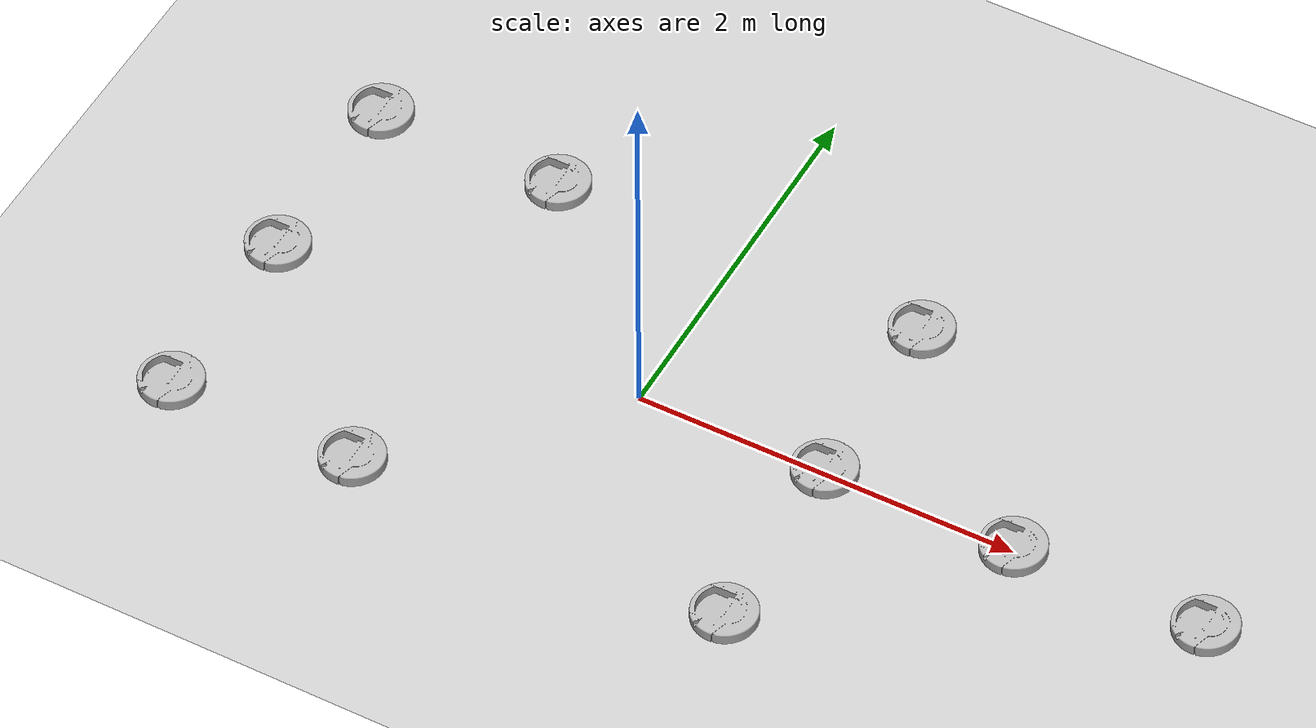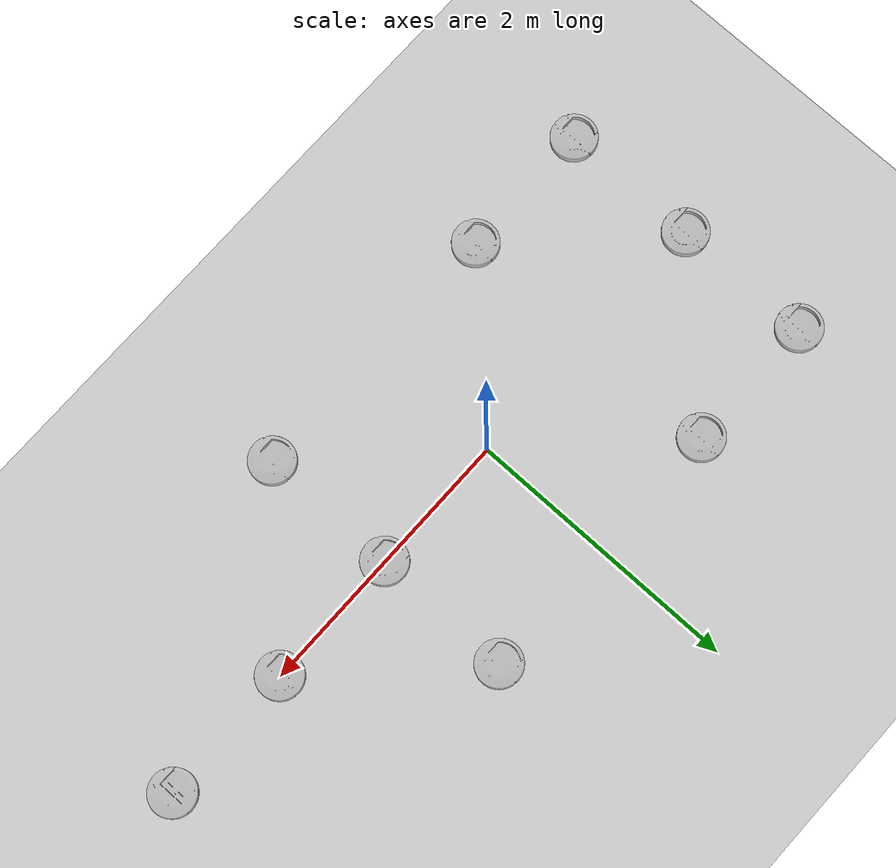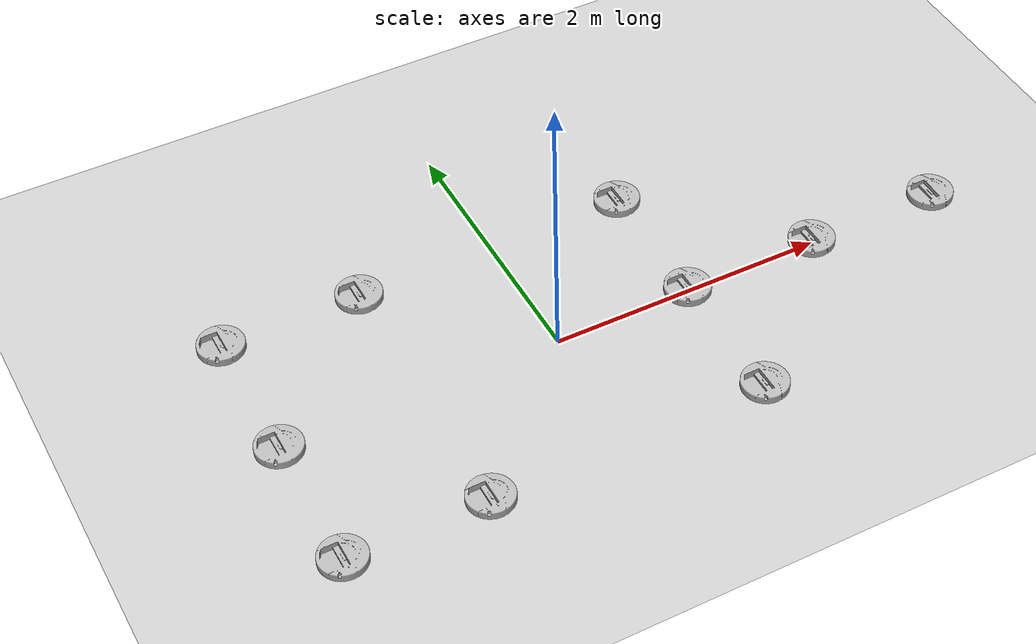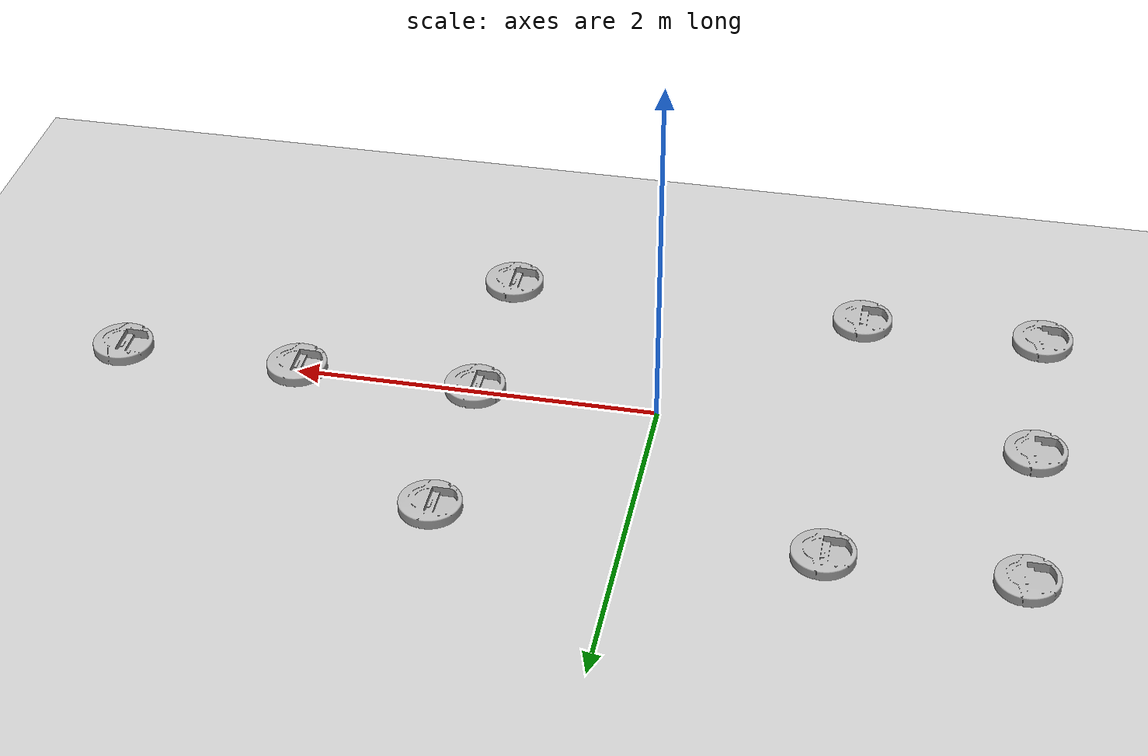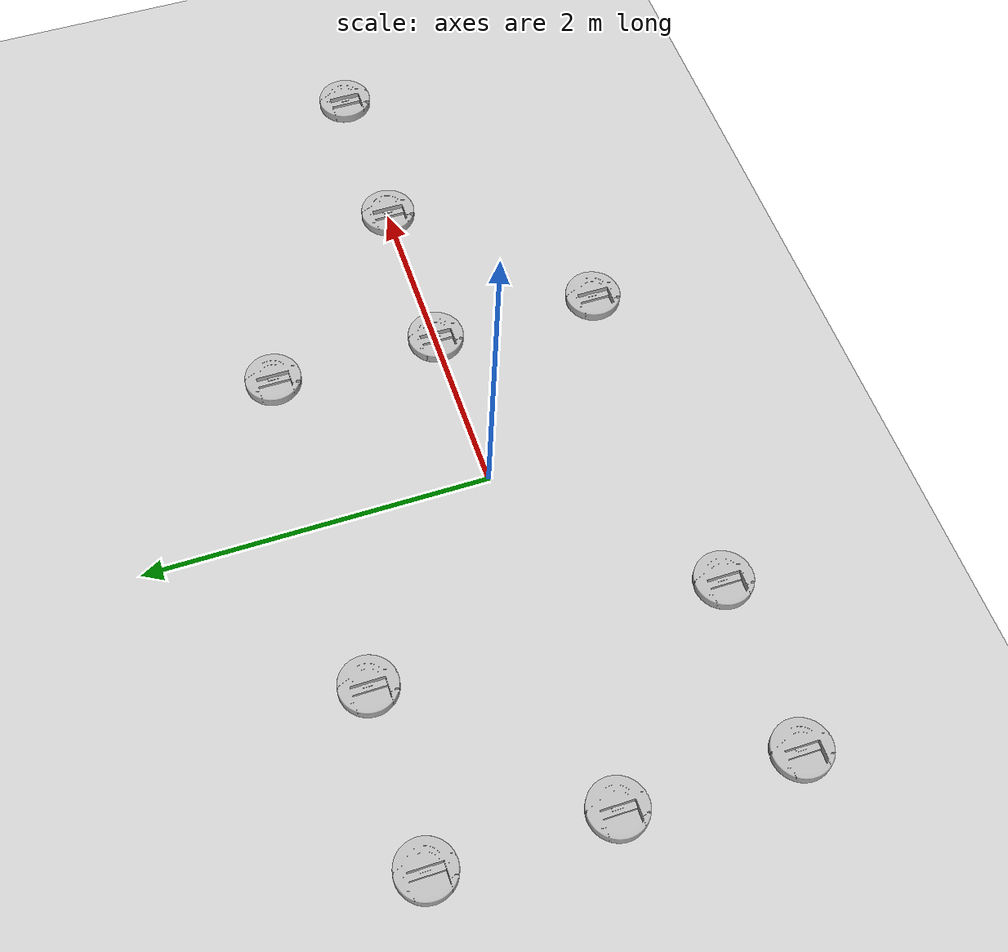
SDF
<sdf version="1.4">
 <world name="default">
  <light name="sun" type="directional">
   <pose>0 0 10 0 -0 0</pose>
   <diffuse>0.8 0.8 0.8 1</diffuse>
   <specular>0.2 0.2 0.2 1</specular>
   <attenuation>
    <range>1000</range>
    <constant>0.9</constant>
    <linear>0.01</linear>
    <quadratic>0.001</quadratic>
   </attenuation>
   <direction>-0.5 0.1 -0.9</direction>
  </light>
  <physics type="ode">
   <max_step_size>0.001</max_step_size>
   <real_time_factor>1</real_time_factor>
   <real_time_update_rate>1000</real_time_update_rate>
   <gravity>0 0 -9.8</gravity>
  </physics>
  <scene><ambient>0.4 0.4 0.4 1</ambient><background>0.7 0.7 0.7 1</background><shadows>1</shadows></scene>
  <model name="iarc-ground">
   <static>1</static>
   <link name="link">
    <collision name="collision">
     <geometry><plane><normal>0 0 1</normal><size>20 20</size></plane></geometry>
     <surface><friction><ode><mu>100</mu><mu2>50</mu2></ode></friction></surface>
    </collision>
    <visual name="visual">
     <cast_shadows>0</cast_shadows>
     <geometry><plane><normal>0 0 1</normal><size>20 20</size></plane></geometry>
     <material>
      <script>
       <uri>model://IARC-ground/materials/scripts</uri>
       <uri>model://IARC-ground/materials/textures</uri>
       <name>IARCGroundPlane/Image</name>
      </script>
     </material>
    </visual>
    <velocity_decay><linear>0</linear><angular>0</angular></velocity_decay>
   </link>
  </model>
  <model name="create">
   <link name="base">
    <inertial>
     <pose>0.001453 -0.000453 0.029787 0 -0 0</pose>
     <inertia>
      <ixx>0.05864</ixx>
      <ixy>0.000124</ixy>
      <ixz>0.000615</ixz>
      <iyy>0.058786</iyy>
      <iyz>1.4e-05</iyz>
      <izz>1.53244</izz>
     </inertia>
     <mass>2.234</mass>
    </inertial>
    <collision name="base_collision">
     <pose>0 0 0.0478 0 -0 0</pose>
     <geometry><cylinder><radius>0.016495</radius><length>0.061163</length></cylinder></geometry>
    </collision>
    <visual name="base_visual">
     <pose>0 0 0.0478 0 -0 0</pose>
     <geometry><mesh><uri>model://create/meshes/create_body.dae</uri></mesh></geometry>
    </visual>
    <collision name="front_wheel_collision">
     <pose>0.13 0 0.017 -2.8814e-12 1.5707 1.5707</pose>
     <geometry><sphere><radius>0.018</radius></sphere></geometry>
     <surface>
      <friction><ode><mu>0</mu><mu2>0</mu2><fdir1>0 0 0</fdir1><slip1>0</slip1><slip2>0</slip2></ode></friction>
     </surface>
    </collision>
    <visual name="front_wheel_visual">
     <pose>0.13 0 0.017 -2.8814e-12 1.5707 1.5707</pose>
     <geometry><sphere><radius>0.009</radius></sphere></geometry>
    </visual>
    <collision name="rear_wheel_collision">
     <pose>-0.13 0 0.017 -2.8814e-12 1.5707 1.5707</pose>
     <geometry><sphere><radius>0.015</radius></sphere></geometry>
     <surface>
      <friction><ode><mu>0</mu><mu2>0</mu2><fdir1>0 0 0</fdir1><slip1>0</slip1><slip2>0</slip2></ode></friction>
     </surface>
    </collision>
    <visual name="rear_wheel_visual">
     <pose>-0.13 0 0.017 -2.8814e-12 1.5707 1.5707</pose>
     <geometry><sphere><radius>0.0075</radius></sphere></geometry>
    </visual>
    <sensor name="left_cliff_sensor" type="ray">
     <pose>0.07 0.14 0.027 0 1.57079 0</pose>
     <ray>
      <scan>
       <horizontal>
        <samples>1</samples>
        <resolution>1</resolution>
        <min_angle>0</min_angle>
        <max_angle>0</max_angle>
       </horizontal>
      </scan>
      <range><min>0.01</min><max>0.04</max><resolution>0.1</resolution></range>
     </ray>
    </sensor>
    <sensor name="leftfront_cliff_sensor" type="ray">
     <pose>0.15 0.04 0.027 0 1.57079 0</pose>
     <ray>
      <scan>
       <horizontal>
        <samples>1</samples>
        <resolution>1</resolution>
        <min_angle>0</min_angle>
        <max_angle>0</max_angle>
       </horizontal>
      </scan>
      <range><min>0.01</min><max>0.04</max><resolution>0.1</resolution></range>
     </ray>
    </sensor>
    <sensor name="right_cliff_sensor" type="ray">
     <pose>0.07 -0.14 0.027 0 1.57079 0</pose>
     <ray>
      <scan>
       <horizontal>
        <samples>1</samples>
        <resolution>1</resolution>
        <min_angle>0</min_angle>
        <max_angle>0</max_angle>
       </horizontal>
      </scan>
      <range><min>0.01</min><max>0.04</max><resolution>0.1</resolution></range>
     </ray>
    </sensor>
    <sensor name="rightfront_cliff_sensor" type="ray">
     <pose>0.15 -0.04 0.027 0 1.57079 0</pose>
     <ray>
      <scan>
       <horizontal>
        <samples>1</samples>
        <resolution>1</resolution>
        <min_angle>0</min_angle>
        <max_angle>0</max_angle>
       </horizontal>
      </scan>
      <range><min>0.01</min><max>0.04</max><resolution>0.1</resolution></range>
     </ray>
    </sensor>
    <sensor name="wall_sensor" type="ray">
     <pose>0.09 -0.12 0.059 0 0 -1</pose>
     <ray>
      <scan>
       <horizontal>
        <samples>1</samples>
        <resolution>1</resolution>
        <min_angle>0</min_angle>
        <max_angle>0</max_angle>
       </horizontal>
      </scan>
      <range><min>0.016</min><max>0.04</max><resolution>0.1</resolution></range>
     </ray>
    </sensor>
    <velocity_decay><linear>0</linear><angular>0</angular></velocity_decay>
   </link>
   <link name="left_wheel">
    <pose>0 0.13 0.032 0 -0 0</pose>
    <inertial>
     <inertia><ixx>0.001</ixx><ixy>0</ixy><ixz>0</ixz><iyy>0.001</iyy><iyz>0</iyz><izz>0.001</izz></inertia>
     <mass>0.01</mass>
    </inertial>
    <collision name="collision">
     <pose>0 0 0 -2.8814e-12 1.5707 1.5707</pose>
     <geometry><cylinder><radius>0.033</radius><length>0.023</length></cylinder></geometry>
     <surface>
      <friction><ode><mu>10</mu><mu2>10</mu2><fdir1>0 0 0</fdir1><slip1>0</slip1><slip2>0</slip2></ode></friction>
     </surface>
    </collision>
    <visual name="visual">
     <pose>0 0 0 -2.8814e-12 1.5707 1.5707</pose>
     <geometry><cylinder><radius>0.033</radius><length>0.023</length></cylinder></geometry>
    </visual>
    <velocity_decay><linear>0</linear><angular>0</angular></velocity_decay>
   </link>
   <link name="right_wheel">
    <pose>0 -0.13 0.032 0 -0 0</pose>
    <inertial>
     <inertia><ixx>0.001</ixx><ixy>0</ixy><ixz>0</ixz><iyy>0.001</iyy><iyz>0</iyz><izz>0.001</izz></inertia>
     <mass>0.01</mass>
    </inertial>
    <collision name="collision">
     <pose>0 0 0 -2.8814e-12 1.5707 1.5707</pose>
     <geometry><cylinder><radius>0.033</radius><length>0.023</length></cylinder></geometry>
     <surface>
      <friction><ode><mu>10</mu><mu2>10</mu2><fdir1>0 0 0</fdir1><slip1>0</slip1><slip2>0</slip2></ode></friction>
     </surface>
    </collision>
    <visual name="visual">
     <pose>0 0 0 -2.8814e-12 1.5707 1.5707</pose>
     <geometry><cylinder><radius>0.033</radius><length>0.023</length></cylinder></geometry>
    </visual>
    <velocity_decay><linear>0</linear><angular>0</angular></velocity_decay>
   </link>
   <joint name="left_wheel" type="revolute">
    <parent>base</parent>
    <child>left_wheel</child>
    <axis><xyz>0 1 0</xyz><limit><lower>-1e+16</lower><upper>1e+16</upper></limit></axis>
   </joint>
   <joint name="right_wheel" type="revolute">
    <parent>base</parent>
    <child>right_wheel</child>
    <axis><xyz>0 1 0</xyz><limit><lower>-1e+16</lower><upper>1e+16</upper></limit></axis>
   </joint>
   <pose>-2 0 0 0 -0 0</pose>
   <static>0</static>
  </model>
  <model name="create_0">
   <link name="base">
    <inertial>
     <pose>0.001453 -0.000453 0.029787 0 -0 0</pose>
     <inertia>
      <ixx>0.05864</ixx>
      <ixy>0.000124</ixy>
      <ixz>0.000615</ixz>
      <iyy>0.058786</iyy>
      <iyz>1.4e-05</iyz>
      <izz>1.53244</izz>
     </inertia>
     <mass>2.234</mass>
    </inertial>
    <collision name="base_collision">
     <pose>0 0 0.0478 0 -0 0</pose>
     <geometry><cylinder><radius>0.016495</radius><length>0.061163</length></cylinder></geometry>
    </collision>
    <visual name="base_visual">
     <pose>0 0 0.0478 0 -0 0</pose>
     <geometry><mesh><uri>model://create/meshes/create_body.dae</uri></mesh></geometry>
    </visual>
    <collision name="front_wheel_collision">
     <pose>0.13 0 0.017 -2.8814e-12 1.5707 1.5707</pose>
     <geometry><sphere><radius>0.018</radius></sphere></geometry>
     <surface>
      <friction><ode><mu>0</mu><mu2>0</mu2><fdir1>0 0 0</fdir1><slip1>0</slip1><slip2>0</slip2></ode></friction>
     </surface>
    </collision>
    <visual name="front_wheel_visual">
     <pose>0.13 0 0.017 -2.8814e-12 1.5707 1.5707</pose>
     <geometry><sphere><radius>0.009</radius></sphere></geometry>
    </visual>
    <collision name="rear_wheel_collision">
     <pose>-0.13 0 0.017 -2.8814e-12 1.5707 1.5707</pose>
     <geometry><sphere><radius>0.015</radius></sphere></geometry>
     <surface>
      <friction><ode><mu>0</mu><mu2>0</mu2><fdir1>0 0 0</fdir1><slip1>0</slip1><slip2>0</slip2></ode></friction>
     </surface>
    </collision>
    <visual name="rear_wheel_visual">
     <pose>-0.13 0 0.017 -2.8814e-12 1.5707 1.5707</pose>
     <geometry><sphere><radius>0.0075</radius></sphere></geometry>
    </visual>
    <sensor name="left_cliff_sensor" type="ray">
     <pose>0.07 0.14 0.027 0 1.57079 0</pose>
     <ray>
      <scan>
       <horizontal>
        <samples>1</samples>
        <resolution>1</resolution>
        <min_angle>0</min_angle>
        <max_angle>0</max_angle>
       </horizontal>
      </scan>
      <range><min>0.01</min><max>0.04</max><resolution>0.1</resolution></range>
     </ray>
    </sensor>
    <sensor name="leftfront_cliff_sensor" type="ray">
     <pose>0.15 0.04 0.027 0 1.57079 0</pose>
     <ray>
      <scan>
       <horizontal>
        <samples>1</samples>
        <resolution>1</resolution>
        <min_angle>0</min_angle>
        <max_angle>0</max_angle>
       </horizontal>
      </scan>
      <range><min>0.01</min><max>0.04</max><resolution>0.1</resolution></range>
     </ray>
    </sensor>
    <sensor name="right_cliff_sensor" type="ray">
     <pose>0.07 -0.14 0.027 0 1.57079 0</pose>
     <ray>
      <scan>
       <horizontal>
        <samples>1</samples>
        <resolution>1</resolution>
        <min_angle>0</min_angle>
        <max_angle>0</max_angle>
       </horizontal>
      </scan>
      <range><min>0.01</min><max>0.04</max><resolution>0.1</resolution></range>
     </ray>
    </sensor>
    <sensor name="rightfront_cliff_sensor" type="ray">
     <pose>0.15 -0.04 0.027 0 1.57079 0</pose>
     <ray>
      <scan>
       <horizontal>
        <samples>1</samples>
        <resolution>1</resolution>
        <min_angle>0</min_angle>
        <max_angle>0</max_angle>
       </horizontal>
      </scan>
      <range><min>0.01</min><max>0.04</max><resolution>0.1</resolution></range>
     </ray>
    </sensor>
    <sensor name="wall_sensor" type="ray">
     <pose>0.09 -0.12 0.059 0 0 -1</pose>
     <ray>
      <scan>
       <horizontal>
        <samples>1</samples>
        <resolution>1</resolution>
        <min_angle>0</min_angle>
        <max_angle>0</max_angle>
       </horizontal>
      </scan>
      <range><min>0.016</min><max>0.04</max><resolution>0.1</resolution></range>
     </ray>
    </sensor>
    <velocity_decay><linear>0</linear><angular>0</angular></velocity_decay>
   </link>
   <link name="left_wheel">
    <pose>0 0.13 0.032 0 -0 0</pose>
    <inertial>
     <inertia><ixx>0.001</ixx><ixy>0</ixy><ixz>0</ixz><iyy>0.001</iyy><iyz>0</iyz><izz>0.001</izz></inertia>
     <mass>0.01</mass>
    </inertial>
    <collision name="collision">
     <pose>0 0 0 -2.8814e-12 1.5707 1.5707</pose>
     <geometry><cylinder><radius>0.033</radius><length>0.023</length></cylinder></geometry>
     <surface>
      <friction><ode><mu>10</mu><mu2>10</mu2><fdir1>0 0 0</fdir1><slip1>0</slip1><slip2>0</slip2></ode></friction>
     </surface>
    </collision>
    <visual name="visual">
     <pose>0 0 0 -2.8814e-12 1.5707 1.5707</pose>
     <geometry><cylinder><radius>0.033</radius><length>0.023</length></cylinder></geometry>
    </visual>
    <velocity_decay><linear>0</linear><angular>0</angular></velocity_decay>
   </link>
   <link name="right_wheel">
    <pose>0 -0.13 0.032 0 -0 0</pose>
    <inertial>
     <inertia><ixx>0.001</ixx><ixy>0</ixy><ixz>0</ixz><iyy>0.001</iyy><iyz>0</iyz><izz>0.001</izz></inertia>
     <mass>0.01</mass>
    </inertial>
    <collision name="collision">
     <pose>0 0 0 -2.8814e-12 1.5707 1.5707</pose>
     <geometry><cylinder><radius>0.033</radius><length>0.023</length></cylinder></geometry>
     <surface>
      <friction><ode><mu>10</mu><mu2>10</mu2><fdir1>0 0 0</fdir1><slip1>0</slip1><slip2>0</slip2></ode></friction>
     </surface>
    </collision>
    <visual name="visual">
     <pose>0 0 0 -2.8814e-12 1.5707 1.5707</pose>
     <geometry><cylinder><radius>0.033</radius><length>0.023</length></cylinder></geometry>
    </visual>
    <velocity_decay><linear>0</linear><angular>0</angular></velocity_decay>
   </link>
   <joint name="left_wheel" type="revolute">
    <parent>base</parent>
    <child>left_wheel</child>
    <axis><xyz>0 1 0</xyz><limit><lower>-1e+16</lower><upper>1e+16</upper></limit></axis>
   </joint>
   <joint name="right_wheel" type="revolute">
    <parent>base</parent>
    <child>right_wheel</child>
    <axis><xyz>0 1 0</xyz><limit><lower>-1e+16</lower><upper>1e+16</upper></limit></axis>
   </joint>
   <pose>2 0 0 0 -0 0</pose>
   <static>0</static>
  </model>
  <model name="create_1">
   <link name="base">
    <inertial>
     <pose>0.001453 -0.000453 0.029787 0 -0 0</pose>
     <inertia>
      <ixx>0.05864</ixx>
      <ixy>0.000124</ixy>
      <ixz>0.000615</ixz>
      <iyy>0.058786</iyy>
      <iyz>1.4e-05</iyz>
      <izz>1.53244</izz>
     </inertia>
     <mass>2.234</mass>
    </inertial>
    <collision name="base_collision">
     <pose>0 0 0.0478 0 -0 0</pose>
     <geometry><cylinder><radius>0.016495</radius><length>0.061163</length></cylinder></geometry>
    </collision>
    <visual name="base_visual">
     <pose>0 0 0.0478 0 -0 0</pose>
     <geometry><mesh><uri>model://create/meshes/create_body.dae</uri></mesh></geometry>
    </visual>
    <collision name="front_wheel_collision">
     <pose>0.13 0 0.017 -2.8814e-12 1.5707 1.5707</pose>
     <geometry><sphere><radius>0.018</radius></sphere></geometry>
     <surface>
      <friction><ode><mu>0</mu><mu2>0</mu2><fdir1>0 0 0</fdir1><slip1>0</slip1><slip2>0</slip2></ode></friction>
     </surface>
    </collision>
    <visual name="front_wheel_visual">
     <pose>0.13 0 0.017 -2.8814e-12 1.5707 1.5707</pose>
     <geometry><sphere><radius>0.009</radius></sphere></geometry>
    </visual>
    <collision name="rear_wheel_collision">
     <pose>-0.13 0 0.017 -2.8814e-12 1.5707 1.5707</pose>
     <geometry><sphere><radius>0.015</radius></sphere></geometry>
     <surface>
      <friction><ode><mu>0</mu><mu2>0</mu2><fdir1>0 0 0</fdir1><slip1>0</slip1><slip2>0</slip2></ode></friction>
     </surface>
    </collision>
    <visual name="rear_wheel_visual">
     <pose>-0.13 0 0.017 -2.8814e-12 1.5707 1.5707</pose>
     <geometry><sphere><radius>0.0075</radius></sphere></geometry>
    </visual>
    <sensor name="left_cliff_sensor" type="ray">
     <pose>0.07 0.14 0.027 0 1.57079 0</pose>
     <ray>
      <scan>
       <horizontal>
        <samples>1</samples>
        <resolution>1</resolution>
        <min_angle>0</min_angle>
        <max_angle>0</max_angle>
       </horizontal>
      </scan>
      <range><min>0.01</min><max>0.04</max><resolution>0.1</resolution></range>
     </ray>
    </sensor>
    <sensor name="leftfront_cliff_sensor" type="ray">
     <pose>0.15 0.04 0.027 0 1.57079 0</pose>
     <ray>
      <scan>
       <horizontal>
        <samples>1</samples>
        <resolution>1</resolution>
        <min_angle>0</min_angle>
        <max_angle>0</max_angle>
       </horizontal>
      </scan>
      <range><min>0.01</min><max>0.04</max><resolution>0.1</resolution></range>
     </ray>
    </sensor>
    <sensor name="right_cliff_sensor" type="ray">
     <pose>0.07 -0.14 0.027 0 1.57079 0</pose>
     <ray>
      <scan>
       <horizontal>
        <samples>1</samples>
        <resolution>1</resolution>
        <min_angle>0</min_angle>
        <max_angle>0</max_angle>
       </horizontal>
      </scan>
      <range><min>0.01</min><max>0.04</max><resolution>0.1</resolution></range>
     </ray>
    </sensor>
    <sensor name="rightfront_cliff_sensor" type="ray">
     <pose>0.15 -0.04 0.027 0 1.57079 0</pose>
     <ray>
      <scan>
       <horizontal>
        <samples>1</samples>
        <resolution>1</resolution>
        <min_angle>0</min_angle>
        <max_angle>0</max_angle>
       </horizontal>
      </scan>
      <range><min>0.01</min><max>0.04</max><resolution>0.1</resolution></range>
     </ray>
    </sensor>
    <sensor name="wall_sensor" type="ray">
     <pose>0.09 -0.12 0.059 0 0 -1</pose>
     <ray>
      <scan>
       <horizontal>
        <samples>1</samples>
        <resolution>1</resolution>
        <min_angle>0</min_angle>
        <max_angle>0</max_angle>
       </horizontal>
      </scan>
      <range><min>0.016</min><max>0.04</max><resolution>0.1</resolution></range>
     </ray>
    </sensor>
    <velocity_decay><linear>0</linear><angular>0</angular></velocity_decay>
   </link>
   <link name="left_wheel">
    <pose>0 0.13 0.032 0 -0 0</pose>
    <inertial>
     <inertia><ixx>0.001</ixx><ixy>0</ixy><ixz>0</ixz><iyy>0.001</iyy><iyz>0</iyz><izz>0.001</izz></inertia>
     <mass>0.01</mass>
    </inertial>
    <collision name="collision">
     <pose>0 0 0 -2.8814e-12 1.5707 1.5707</pose>
     <geometry><cylinder><radius>0.033</radius><length>0.023</length></cylinder></geometry>
     <surface>
      <friction><ode><mu>10</mu><mu2>10</mu2><fdir1>0 0 0</fdir1><slip1>0</slip1><slip2>0</slip2></ode></friction>
     </surface>
    </collision>
    <visual name="visual">
     <pose>0 0 0 -2.8814e-12 1.5707 1.5707</pose>
     <geometry><cylinder><radius>0.033</radius><length>0.023</length></cylinder></geometry>
    </visual>
    <velocity_decay><linear>0</linear><angular>0</angular></velocity_decay>
   </link>
   <link name="right_wheel">
    <pose>0 -0.13 0.032 0 -0 0</pose>
    <inertial>
     <inertia><ixx>0.001</ixx><ixy>0</ixy><ixz>0</ixz><iyy>0.001</iyy><iyz>0</iyz><izz>0.001</izz></inertia>
     <mass>0.01</mass>
    </inertial>
    <collision name="collision">
     <pose>0 0 0 -2.8814e-12 1.5707 1.5707</pose>
     <geometry><cylinder><radius>0.033</radius><length>0.023</length></cylinder></geometry>
     <surface>
      <friction><ode><mu>10</mu><mu2>10</mu2><fdir1>0 0 0</fdir1><slip1>0</slip1><slip2>0</slip2></ode></friction>
     </surface>
    </collision>
    <visual name="visual">
     <pose>0 0 0 -2.8814e-12 1.5707 1.5707</pose>
     <geometry><cylinder><radius>0.033</radius><length>0.023</length></cylinder></geometry>
    </visual>
    <velocity_decay><linear>0</linear><angular>0</angular></velocity_decay>
   </link>
   <joint name="left_wheel" type="revolute">
    <parent>base</parent>
    <child>left_wheel</child>
    <axis><xyz>0 1 0</xyz><limit><lower>-1e+16</lower><upper>1e+16</upper></limit></axis>
   </joint>
   <joint name="right_wheel" type="revolute">
    <parent>base</parent>
    <child>right_wheel</child>
    <axis><xyz>0 1 0</xyz><limit><lower>-1e+16</lower><upper>1e+16</upper></limit></axis>
   </joint>
   <pose>1 0 0 0 -0 0</pose>
   <static>0</static>
  </model>
  <model name="create_2">
   <link name="base">
    <inertial>
     <pose>0.001453 -0.000453 0.029787 0 -0 0</pose>
     <inertia>
      <ixx>0.05864</ixx>
      <ixy>0.000124</ixy>
      <ixz>0.000615</ixz>
      <iyy>0.058786</iyy>
      <iyz>1.4e-05</iyz>
      <izz>1.53244</izz>
     </inertia>
     <mass>2.234</mass>
    </inertial>
    <collision name="base_collision">
     <pose>0 0 0.0478 0 -0 0</pose>
     <geometry><cylinder><radius>0.016495</radius><length>0.061163</length></cylinder></geometry>
    </collision>
    <visual name="base_visual">
     <pose>0 0 0.0478 0 -0 0</pose>
     <geometry><mesh><uri>model://create/meshes/create_body.dae</uri></mesh></geometry>
    </visual>
    <collision name="front_wheel_collision">
     <pose>0.13 0 0.017 -2.8814e-12 1.5707 1.5707</pose>
     <geometry><sphere><radius>0.018</radius></sphere></geometry>
     <surface>
      <friction><ode><mu>0</mu><mu2>0</mu2><fdir1>0 0 0</fdir1><slip1>0</slip1><slip2>0</slip2></ode></friction>
     </surface>
    </collision>
    <visual name="front_wheel_visual">
     <pose>0.13 0 0.017 -2.8814e-12 1.5707 1.5707</pose>
     <geometry><sphere><radius>0.009</radius></sphere></geometry>
    </visual>
    <collision name="rear_wheel_collision">
     <pose>-0.13 0 0.017 -2.8814e-12 1.5707 1.5707</pose>
     <geometry><sphere><radius>0.015</radius></sphere></geometry>
     <surface>
      <friction><ode><mu>0</mu><mu2>0</mu2><fdir1>0 0 0</fdir1><slip1>0</slip1><slip2>0</slip2></ode></friction>
     </surface>
    </collision>
    <visual name="rear_wheel_visual">
     <pose>-0.13 0 0.017 -2.8814e-12 1.5707 1.5707</pose>
     <geometry><sphere><radius>0.0075</radius></sphere></geometry>
    </visual>
    <sensor name="left_cliff_sensor" type="ray">
     <pose>0.07 0.14 0.027 0 1.57079 0</pose>
     <ray>
      <scan>
       <horizontal>
        <samples>1</samples>
        <resolution>1</resolution>
        <min_angle>0</min_angle>
        <max_angle>0</max_angle>
       </horizontal>
      </scan>
      <range><min>0.01</min><max>0.04</max><resolution>0.1</resolution></range>
     </ray>
    </sensor>
    <sensor name="leftfront_cliff_sensor" type="ray">
     <pose>0.15 0.04 0.027 0 1.57079 0</pose>
     <ray>
      <scan>
       <horizontal>
        <samples>1</samples>
        <resolution>1</resolution>
        <min_angle>0</min_angle>
        <max_angle>0</max_angle>
       </horizontal>
      </scan>
      <range><min>0.01</min><max>0.04</max><resolution>0.1</resolution></range>
     </ray>
    </sensor>
    <sensor name="right_cliff_sensor" type="ray">
     <pose>0.07 -0.14 0.027 0 1.57079 0</pose>
     <ray>
      <scan>
       <horizontal>
        <samples>1</samples>
        <resolution>1</resolution>
        <min_angle>0</min_angle>
        <max_angle>0</max_angle>
       </horizontal>
      </scan>
      <range><min>0.01</min><max>0.04</max><resolution>0.1</resolution></range>
     </ray>
    </sensor>
    <sensor name="rightfront_cliff_sensor" type="ray">
     <pose>0.15 -0.04 0.027 0 1.57079 0</pose>
     <ray>
      <scan>
       <horizontal>
        <samples>1</samples>
        <resolution>1</resolution>
        <min_angle>0</min_angle>
        <max_angle>0</max_angle>
       </horizontal>
      </scan>
      <range><min>0.01</min><max>0.04</max><resolution>0.1</resolution></range>
     </ray>
    </sensor>
    <sensor name="wall_sensor" type="ray">
     <pose>0.09 -0.12 0.059 0 0 -1</pose>
     <ray>
      <scan>
       <horizontal>
        <samples>1</samples>
        <resolution>1</resolution>
        <min_angle>0</min_angle>
        <max_angle>0</max_angle>
       </horizontal>
      </scan>
      <range><min>0.016</min><max>0.04</max><resolution>0.1</resolution></range>
     </ray>
    </sensor>
    <velocity_decay><linear>0</linear><angular>0</angular></velocity_decay>
   </link>
   <link name="left_wheel">
    <pose>0 0.13 0.032 0 -0 0</pose>
    <inertial>
     <inertia><ixx>0.001</ixx><ixy>0</ixy><ixz>0</ixz><iyy>0.001</iyy><iyz>0</iyz><izz>0.001</izz></inertia>
     <mass>0.01</mass>
    </inertial>
    <collision name="collision">
     <pose>0 0 0 -2.8814e-12 1.5707 1.5707</pose>
     <geometry><cylinder><radius>0.033</radius><length>0.023</length></cylinder></geometry>
     <surface>
      <friction><ode><mu>10</mu><mu2>10</mu2><fdir1>0 0 0</fdir1><slip1>0</slip1><slip2>0</slip2></ode></friction>
     </surface>
    </collision>
    <visual name="visual">
     <pose>0 0 0 -2.8814e-12 1.5707 1.5707</pose>
     <geometry><cylinder><radius>0.033</radius><length>0.023</length></cylinder></geometry>
    </visual>
    <velocity_decay><linear>0</linear><angular>0</angular></velocity_decay>
   </link>
   <link name="right_wheel">
    <pose>0 -0.13 0.032 0 -0 0</pose>
    <inertial>
     <inertia><ixx>0.001</ixx><ixy>0</ixy><ixz>0</ixz><iyy>0.001</iyy><iyz>0</iyz><izz>0.001</izz></inertia>
     <mass>0.01</mass>
    </inertial>
    <collision name="collision">
     <pose>0 0 0 -2.8814e-12 1.5707 1.5707</pose>
     <geometry><cylinder><radius>0.033</radius><length>0.023</length></cylinder></geometry>
     <surface>
      <friction><ode><mu>10</mu><mu2>10</mu2><fdir1>0 0 0</fdir1><slip1>0</slip1><slip2>0</slip2></ode></friction>
     </surface>
    </collision>
    <visual name="visual">
     <pose>0 0 0 -2.8814e-12 1.5707 1.5707</pose>
     <geometry><cylinder><radius>0.033</radius><length>0.023</length></cylinder></geometry>
    </visual>
    <velocity_decay><linear>0</linear><angular>0</angular></velocity_decay>
   </link>
   <joint name="left_wheel" type="revolute">
    <parent>base</parent>
    <child>left_wheel</child>
    <axis><xyz>0 1 0</xyz><limit><lower>-1e+16</lower><upper>1e+16</upper></limit></axis>
   </joint>
   <joint name="right_wheel" type="revolute">
    <parent>base</parent>
    <child>right_wheel</child>
    <axis><xyz>0 1 0</xyz><limit><lower>-1e+16</lower><upper>1e+16</upper></limit></axis>
   </joint>
   <pose>-2 -1 0 0 -0 0</pose>
   <static>0</static>
  </model>
  <model name="create_3">
   <link name="base">
    <inertial>
     <pose>0.001453 -0.000453 0.029787 0 -0 0</pose>
     <inertia>
      <ixx>0.05864</ixx>
      <ixy>0.000124</ixy>
      <ixz>0.000615</ixz>
      <iyy>0.058786</iyy>
      <iyz>1.4e-05</iyz>
      <izz>1.53244</izz>
     </inertia>
     <mass>2.234</mass>
    </inertial>
    <collision name="base_collision">
     <pose>0 0 0.0478 0 -0 0</pose>
     <geometry><cylinder><radius>0.016495</radius><length>0.061163</length></cylinder></geometry>
    </collision>
    <visual name="base_visual">
     <pose>0 0 0.0478 0 -0 0</pose>
     <geometry><mesh><uri>model://create/meshes/create_body.dae</uri></mesh></geometry>
    </visual>
    <collision name="front_wheel_collision">
     <pose>0.13 0 0.017 -2.8814e-12 1.5707 1.5707</pose>
     <geometry><sphere><radius>0.018</radius></sphere></geometry>
     <surface>
      <friction><ode><mu>0</mu><mu2>0</mu2><fdir1>0 0 0</fdir1><slip1>0</slip1><slip2>0</slip2></ode></friction>
     </surface>
    </collision>
    <visual name="front_wheel_visual">
     <pose>0.13 0 0.017 -2.8814e-12 1.5707 1.5707</pose>
     <geometry><sphere><radius>0.009</radius></sphere></geometry>
    </visual>
    <collision name="rear_wheel_collision">
     <pose>-0.13 0 0.017 -2.8814e-12 1.5707 1.5707</pose>
     <geometry><sphere><radius>0.015</radius></sphere></geometry>
     <surface>
      <friction><ode><mu>0</mu><mu2>0</mu2><fdir1>0 0 0</fdir1><slip1>0</slip1><slip2>0</slip2></ode></friction>
     </surface>
    </collision>
    <visual name="rear_wheel_visual">
     <pose>-0.13 0 0.017 -2.8814e-12 1.5707 1.5707</pose>
     <geometry><sphere><radius>0.0075</radius></sphere></geometry>
    </visual>
    <sensor name="left_cliff_sensor" type="ray">
     <pose>0.07 0.14 0.027 0 1.57079 0</pose>
     <ray>
      <scan>
       <horizontal>
        <samples>1</samples>
        <resolution>1</resolution>
        <min_angle>0</min_angle>
        <max_angle>0</max_angle>
       </horizontal>
      </scan>
      <range><min>0.01</min><max>0.04</max><resolution>0.1</resolution></range>
     </ray>
    </sensor>
    <sensor name="leftfront_cliff_sensor" type="ray">
     <pose>0.15 0.04 0.027 0 1.57079 0</pose>
     <ray>
      <scan>
       <horizontal>
        <samples>1</samples>
        <resolution>1</resolution>
        <min_angle>0</min_angle>
        <max_angle>0</max_angle>
       </horizontal>
      </scan>
      <range><min>0.01</min><max>0.04</max><resolution>0.1</resolution></range>
     </ray>
    </sensor>
    <sensor name="right_cliff_sensor" type="ray">
     <pose>0.07 -0.14 0.027 0 1.57079 0</pose>
     <ray>
      <scan>
       <horizontal>
        <samples>1</samples>
        <resolution>1</resolution>
        <min_angle>0</min_angle>
        <max_angle>0</max_angle>
       </horizontal>
      </scan>
      <range><min>0.01</min><max>0.04</max><resolution>0.1</resolution></range>
     </ray>
    </sensor>
    <sensor name="rightfront_cliff_sensor" type="ray">
     <pose>0.15 -0.04 0.027 0 1.57079 0</pose>
     <ray>
      <scan>
       <horizontal>
        <samples>1</samples>
        <resolution>1</resolution>
        <min_angle>0</min_angle>
        <max_angle>0</max_angle>
       </horizontal>
      </scan>
      <range><min>0.01</min><max>0.04</max><resolution>0.1</resolution></range>
     </ray>
    </sensor>
    <sensor name="wall_sensor" type="ray">
     <pose>0.09 -0.12 0.059 0 0 -1</pose>
     <ray>
      <scan>
       <horizontal>
        <samples>1</samples>
        <resolution>1</resolution>
        <min_angle>0</min_angle>
        <max_angle>0</max_angle>
       </horizontal>
      </scan>
      <range><min>0.016</min><max>0.04</max><resolution>0.1</resolution></range>
     </ray>
    </sensor>
    <velocity_decay><linear>0</linear><angular>0</angular></velocity_decay>
   </link>
   <link name="left_wheel">
    <pose>0 0.13 0.032 0 -0 0</pose>
    <inertial>
     <inertia><ixx>0.001</ixx><ixy>0</ixy><ixz>0</ixz><iyy>0.001</iyy><iyz>0</iyz><izz>0.001</izz></inertia>
     <mass>0.01</mass>
    </inertial>
    <collision name="collision">
     <pose>0 0 0 -2.8814e-12 1.5707 1.5707</pose>
     <geometry><cylinder><radius>0.033</radius><length>0.023</length></cylinder></geometry>
     <surface>
      <friction><ode><mu>10</mu><mu2>10</mu2><fdir1>0 0 0</fdir1><slip1>0</slip1><slip2>0</slip2></ode></friction>
     </surface>
    </collision>
    <visual name="visual">
     <pose>0 0 0 -2.8814e-12 1.5707 1.5707</pose>
     <geometry><cylinder><radius>0.033</radius><length>0.023</length></cylinder></geometry>
    </visual>
    <velocity_decay><linear>0</linear><angular>0</angular></velocity_decay>
   </link>
   <link name="right_wheel">
    <pose>0 -0.13 0.032 0 -0 0</pose>
    <inertial>
     <inertia><ixx>0.001</ixx><ixy>0</ixy><ixz>0</ixz><iyy>0.001</iyy><iyz>0</iyz><izz>0.001</izz></inertia>
     <mass>0.01</mass>
    </inertial>
    <collision name="collision">
     <pose>0 0 0 -2.8814e-12 1.5707 1.5707</pose>
     <geometry><cylinder><radius>0.033</radius><length>0.023</length></cylinder></geometry>
     <surface>
      <friction><ode><mu>10</mu><mu2>10</mu2><fdir1>0 0 0</fdir1><slip1>0</slip1><slip2>0</slip2></ode></friction>
     </surface>
    </collision>
    <visual name="visual">
     <pose>0 0 0 -2.8814e-12 1.5707 1.5707</pose>
     <geometry><cylinder><radius>0.033</radius><length>0.023</length></cylinder></geometry>
    </visual>
    <velocity_decay><linear>0</linear><angular>0</angular></velocity_decay>
   </link>
   <joint name="left_wheel" type="revolute">
    <parent>base</parent>
    <child>left_wheel</child>
    <axis><xyz>0 1 0</xyz><limit><lower>-1e+16</lower><upper>1e+16</upper></limit></axis>
   </joint>
   <joint name="right_wheel" type="revolute">
    <parent>base</parent>
    <child>right_wheel</child>
    <axis><xyz>0 1 0</xyz><limit><lower>-1e+16</lower><upper>1e+16</upper></limit></axis>
   </joint>
   <pose>-1 -1 0 0 -0 0</pose>
   <static>0</static>
  </model>
  <model name="create_4">
   <link name="base">
    <inertial>
     <pose>0.001453 -0.000453 0.029787 0 -0 0</pose>
     <inertia>
      <ixx>0.05864</ixx>
      <ixy>0.000124</ixy>
      <ixz>0.000615</ixz>
      <iyy>0.058786</iyy>
      <iyz>1.4e-05</iyz>
      <izz>1.53244</izz>
     </inertia>
     <mass>2.234</mass>
    </inertial>
    <collision name="base_collision">
     <pose>0 0 0.0478 0 -0 0</pose>
     <geometry><cylinder><radius>0.016495</radius><length>0.061163</length></cylinder></geometry>
    </collision>
    <visual name="base_visual">
     <pose>0 0 0.0478 0 -0 0</pose>
     <geometry><mesh><uri>model://create/meshes/create_body.dae</uri></mesh></geometry>
    </visual>
    <collision name="front_wheel_collision">
     <pose>0.13 0 0.017 -2.8814e-12 1.5707 1.5707</pose>
     <geometry><sphere><radius>0.018</radius></sphere></geometry>
     <surface>
      <friction><ode><mu>0</mu><mu2>0</mu2><fdir1>0 0 0</fdir1><slip1>0</slip1><slip2>0</slip2></ode></friction>
     </surface>
    </collision>
    <visual name="front_wheel_visual">
     <pose>0.13 0 0.017 -2.8814e-12 1.5707 1.5707</pose>
     <geometry><sphere><radius>0.009</radius></sphere></geometry>
    </visual>
    <collision name="rear_wheel_collision">
     <pose>-0.13 0 0.017 -2.8814e-12 1.5707 1.5707</pose>
     <geometry><sphere><radius>0.015</radius></sphere></geometry>
     <surface>
      <friction><ode><mu>0</mu><mu2>0</mu2><fdir1>0 0 0</fdir1><slip1>0</slip1><slip2>0</slip2></ode></friction>
     </surface>
    </collision>
    <visual name="rear_wheel_visual">
     <pose>-0.13 0 0.017 -2.8814e-12 1.5707 1.5707</pose>
     <geometry><sphere><radius>0.0075</radius></sphere></geometry>
    </visual>
    <sensor name="left_cliff_sensor" type="ray">
     <pose>0.07 0.14 0.027 0 1.57079 0</pose>
     <ray>
      <scan>
       <horizontal>
        <samples>1</samples>
        <resolution>1</resolution>
        <min_angle>0</min_angle>
        <max_angle>0</max_angle>
       </horizontal>
      </scan>
      <range><min>0.01</min><max>0.04</max><resolution>0.1</resolution></range>
     </ray>
    </sensor>
    <sensor name="leftfront_cliff_sensor" type="ray">
     <pose>0.15 0.04 0.027 0 1.57079 0</pose>
     <ray>
      <scan>
       <horizontal>
        <samples>1</samples>
        <resolution>1</resolution>
        <min_angle>0</min_angle>
        <max_angle>0</max_angle>
       </horizontal>
      </scan>
      <range><min>0.01</min><max>0.04</max><resolution>0.1</resolution></range>
     </ray>
    </sensor>
    <sensor name="right_cliff_sensor" type="ray">
     <pose>0.07 -0.14 0.027 0 1.57079 0</pose>
     <ray>
      <scan>
       <horizontal>
        <samples>1</samples>
        <resolution>1</resolution>
        <min_angle>0</min_angle>
        <max_angle>0</max_angle>
       </horizontal>
      </scan>
      <range><min>0.01</min><max>0.04</max><resolution>0.1</resolution></range>
     </ray>
    </sensor>
    <sensor name="rightfront_cliff_sensor" type="ray">
     <pose>0.15 -0.04 0.027 0 1.57079 0</pose>
     <ray>
      <scan>
       <horizontal>
        <samples>1</samples>
        <resolution>1</resolution>
        <min_angle>0</min_angle>
        <max_angle>0</max_angle>
       </horizontal>
      </scan>
      <range><min>0.01</min><max>0.04</max><resolution>0.1</resolution></range>
     </ray>
    </sensor>
    <sensor name="wall_sensor" type="ray">
     <pose>0.09 -0.12 0.059 0 0 -1</pose>
     <ray>
      <scan>
       <horizontal>
        <samples>1</samples>
        <resolution>1</resolution>
        <min_angle>0</min_angle>
        <max_angle>0</max_angle>
       </horizontal>
      </scan>
      <range><min>0.016</min><max>0.04</max><resolution>0.1</resolution></range>
     </ray>
    </sensor>
    <velocity_decay><linear>0</linear><angular>0</angular></velocity_decay>
   </link>
   <link name="left_wheel">
    <pose>0 0.13 0.032 0 -0 0</pose>
    <inertial>
     <inertia><ixx>0.001</ixx><ixy>0</ixy><ixz>0</ixz><iyy>0.001</iyy><iyz>0</iyz><izz>0.001</izz></inertia>
     <mass>0.01</mass>
    </inertial>
    <collision name="collision">
     <pose>0 0 0 -2.8814e-12 1.5707 1.5707</pose>
     <geometry><cylinder><radius>0.033</radius><length>0.023</length></cylinder></geometry>
     <surface>
      <friction><ode><mu>10</mu><mu2>10</mu2><fdir1>0 0 0</fdir1><slip1>0</slip1><slip2>0</slip2></ode></friction>
     </surface>
    </collision>
    <visual name="visual">
     <pose>0 0 0 -2.8814e-12 1.5707 1.5707</pose>
     <geometry><cylinder><radius>0.033</radius><length>0.023</length></cylinder></geometry>
    </visual>
    <velocity_decay><linear>0</linear><angular>0</angular></velocity_decay>
   </link>
   <link name="right_wheel">
    <pose>0 -0.13 0.032 0 -0 0</pose>
    <inertial>
     <inertia><ixx>0.001</ixx><ixy>0</ixy><ixz>0</ixz><iyy>0.001</iyy><iyz>0</iyz><izz>0.001</izz></inertia>
     <mass>0.01</mass>
    </inertial>
    <collision name="collision">
     <pose>0 0 0 -2.8814e-12 1.5707 1.5707</pose>
     <geometry><cylinder><radius>0.033</radius><length>0.023</length></cylinder></geometry>
     <surface>
      <friction><ode><mu>10</mu><mu2>10</mu2><fdir1>0 0 0</fdir1><slip1>0</slip1><slip2>0</slip2></ode></friction>
     </surface>
    </collision>
    <visual name="visual">
     <pose>0 0 0 -2.8814e-12 1.5707 1.5707</pose>
     <geometry><cylinder><radius>0.033</radius><length>0.023</length></cylinder></geometry>
    </visual>
    <velocity_decay><linear>0</linear><angular>0</angular></velocity_decay>
   </link>
   <joint name="left_wheel" type="revolute">
    <parent>base</parent>
    <child>left_wheel</child>
    <axis><xyz>0 1 0</xyz><limit><lower>-1e+16</lower><upper>1e+16</upper></limit></axis>
   </joint>
   <joint name="right_wheel" type="revolute">
    <parent>base</parent>
    <child>right_wheel</child>
    <axis><xyz>0 1 0</xyz><limit><lower>-1e+16</lower><upper>1e+16</upper></limit></axis>
   </joint>
   <pose>-2 1 0 0 -0 0</pose>
   <static>0</static>
  </model>
  <model name="create_5">
   <link name="base">
    <inertial>
     <pose>0.001453 -0.000453 0.029787 0 -0 0</pose>
     <inertia>
      <ixx>0.05864</ixx>
      <ixy>0.000124</ixy>
      <ixz>0.000615</ixz>
      <iyy>0.058786</iyy>
      <iyz>1.4e-05</iyz>
      <izz>1.53244</izz>
     </inertia>
     <mass>2.234</mass>
    </inertial>
    <collision name="base_collision">
     <pose>0 0 0.0478 0 -0 0</pose>
     <geometry><cylinder><radius>0.016495</radius><length>0.061163</length></cylinder></geometry>
    </collision>
    <visual name="base_visual">
     <pose>0 0 0.0478 0 -0 0</pose>
     <geometry><mesh><uri>model://create/meshes/create_body.dae</uri></mesh></geometry>
    </visual>
    <collision name="front_wheel_collision">
     <pose>0.13 0 0.017 -2.8814e-12 1.5707 1.5707</pose>
     <geometry><sphere><radius>0.018</radius></sphere></geometry>
     <surface>
      <friction><ode><mu>0</mu><mu2>0</mu2><fdir1>0 0 0</fdir1><slip1>0</slip1><slip2>0</slip2></ode></friction>
     </surface>
    </collision>
    <visual name="front_wheel_visual">
     <pose>0.13 0 0.017 -2.8814e-12 1.5707 1.5707</pose>
     <geometry><sphere><radius>0.009</radius></sphere></geometry>
    </visual>
    <collision name="rear_wheel_collision">
     <pose>-0.13 0 0.017 -2.8814e-12 1.5707 1.5707</pose>
     <geometry><sphere><radius>0.015</radius></sphere></geometry>
     <surface>
      <friction><ode><mu>0</mu><mu2>0</mu2><fdir1>0 0 0</fdir1><slip1>0</slip1><slip2>0</slip2></ode></friction>
     </surface>
    </collision>
    <visual name="rear_wheel_visual">
     <pose>-0.13 0 0.017 -2.8814e-12 1.5707 1.5707</pose>
     <geometry><sphere><radius>0.0075</radius></sphere></geometry>
    </visual>
    <sensor name="left_cliff_sensor" type="ray">
     <pose>0.07 0.14 0.027 0 1.57079 0</pose>
     <ray>
      <scan>
       <horizontal>
        <samples>1</samples>
        <resolution>1</resolution>
        <min_angle>0</min_angle>
        <max_angle>0</max_angle>
       </horizontal>
      </scan>
      <range><min>0.01</min><max>0.04</max><resolution>0.1</resolution></range>
     </ray>
    </sensor>
    <sensor name="leftfront_cliff_sensor" type="ray">
     <pose>0.15 0.04 0.027 0 1.57079 0</pose>
     <ray>
      <scan>
       <horizontal>
        <samples>1</samples>
        <resolution>1</resolution>
        <min_angle>0</min_angle>
        <max_angle>0</max_angle>
       </horizontal>
      </scan>
      <range><min>0.01</min><max>0.04</max><resolution>0.1</resolution></range>
     </ray>
    </sensor>
    <sensor name="right_cliff_sensor" type="ray">
     <pose>0.07 -0.14 0.027 0 1.57079 0</pose>
     <ray>
      <scan>
       <horizontal>
        <samples>1</samples>
        <resolution>1</resolution>
        <min_angle>0</min_angle>
        <max_angle>0</max_angle>
       </horizontal>
      </scan>
      <range><min>0.01</min><max>0.04</max><resolution>0.1</resolution></range>
     </ray>
    </sensor>
    <sensor name="rightfront_cliff_sensor" type="ray">
     <pose>0.15 -0.04 0.027 0 1.57079 0</pose>
     <ray>
      <scan>
       <horizontal>
        <samples>1</samples>
        <resolution>1</resolution>
        <min_angle>0</min_angle>
        <max_angle>0</max_angle>
       </horizontal>
      </scan>
      <range><min>0.01</min><max>0.04</max><resolution>0.1</resolution></range>
     </ray>
    </sensor>
    <sensor name="wall_sensor" type="ray">
     <pose>0.09 -0.12 0.059 0 0 -1</pose>
     <ray>
      <scan>
       <horizontal>
        <samples>1</samples>
        <resolution>1</resolution>
        <min_angle>0</min_angle>
        <max_angle>0</max_angle>
       </horizontal>
      </scan>
      <range><min>0.016</min><max>0.04</max><resolution>0.1</resolution></range>
     </ray>
    </sensor>
    <velocity_decay><linear>0</linear><angular>0</angular></velocity_decay>
   </link>
   <link name="left_wheel">
    <pose>0 0.13 0.032 0 -0 0</pose>
    <inertial>
     <inertia><ixx>0.001</ixx><ixy>0</ixy><ixz>0</ixz><iyy>0.001</iyy><iyz>0</iyz><izz>0.001</izz></inertia>
     <mass>0.01</mass>
    </inertial>
    <collision name="collision">
     <pose>0 0 0 -2.8814e-12 1.5707 1.5707</pose>
     <geometry><cylinder><radius>0.033</radius><length>0.023</length></cylinder></geometry>
     <surface>
      <friction><ode><mu>10</mu><mu2>10</mu2><fdir1>0 0 0</fdir1><slip1>0</slip1><slip2>0</slip2></ode></friction>
     </surface>
    </collision>
    <visual name="visual">
     <pose>0 0 0 -2.8814e-12 1.5707 1.5707</pose>
     <geometry><cylinder><radius>0.033</radius><length>0.023</length></cylinder></geometry>
    </visual>
    <velocity_decay><linear>0</linear><angular>0</angular></velocity_decay>
   </link>
   <link name="right_wheel">
    <pose>0 -0.13 0.032 0 -0 0</pose>
    <inertial>
     <inertia><ixx>0.001</ixx><ixy>0</ixy><ixz>0</ixz><iyy>0.001</iyy><iyz>0</iyz><izz>0.001</izz></inertia>
     <mass>0.01</mass>
    </inertial>
    <collision name="collision">
     <pose>0 0 0 -2.8814e-12 1.5707 1.5707</pose>
     <geometry><cylinder><radius>0.033</radius><length>0.023</length></cylinder></geometry>
     <surface>
      <friction><ode><mu>10</mu><mu2>10</mu2><fdir1>0 0 0</fdir1><slip1>0</slip1><slip2>0</slip2></ode></friction>
     </surface>
    </collision>
    <visual name="visual">
     <pose>0 0 0 -2.8814e-12 1.5707 1.5707</pose>
     <geometry><cylinder><radius>0.033</radius><length>0.023</length></cylinder></geometry>
    </visual>
    <velocity_decay><linear>0</linear><angular>0</angular></velocity_decay>
   </link>
   <joint name="left_wheel" type="revolute">
    <parent>base</parent>
    <child>left_wheel</child>
    <axis><xyz>0 1 0</xyz><limit><lower>-1e+16</lower><upper>1e+16</upper></limit></axis>
   </joint>
   <joint name="right_wheel" type="revolute">
    <parent>base</parent>
    <child>right_wheel</child>
    <axis><xyz>0 1 0</xyz><limit><lower>-1e+16</lower><upper>1e+16</upper></limit></axis>
   </joint>
   <pose>-1 1 0 0 -0 0</pose>
   <static>0</static>
  </model>
  <model name="create_6">
   <link name="base">
    <inertial>
     <pose>0.001453 -0.000453 0.029787 0 -0 0</pose>
     <inertia>
      <ixx>0.05864</ixx>
      <ixy>0.000124</ixy>
      <ixz>0.000615</ixz>
      <iyy>0.058786</iyy>
      <iyz>1.4e-05</iyz>
      <izz>1.53244</izz>
     </inertia>
     <mass>2.234</mass>
    </inertial>
    <collision name="base_collision">
     <pose>0 0 0.0478 0 -0 0</pose>
     <geometry><cylinder><radius>0.016495</radius><length>0.061163</length></cylinder></geometry>
    </collision>
    <visual name="base_visual">
     <pose>0 0 0.0478 0 -0 0</pose>
     <geometry><mesh><uri>model://create/meshes/create_body.dae</uri></mesh></geometry>
    </visual>
    <collision name="front_wheel_collision">
     <pose>0.13 0 0.017 -2.8814e-12 1.5707 1.5707</pose>
     <geometry><sphere><radius>0.018</radius></sphere></geometry>
     <surface>
      <friction><ode><mu>0</mu><mu2>0</mu2><fdir1>0 0 0</fdir1><slip1>0</slip1><slip2>0</slip2></ode></friction>
     </surface>
    </collision>
    <visual name="front_wheel_visual">
     <pose>0.13 0 0.017 -2.8814e-12 1.5707 1.5707</pose>
     <geometry><sphere><radius>0.009</radius></sphere></geometry>
    </visual>
    <collision name="rear_wheel_collision">
     <pose>-0.13 0 0.017 -2.8814e-12 1.5707 1.5707</pose>
     <geometry><sphere><radius>0.015</radius></sphere></geometry>
     <surface>
      <friction><ode><mu>0</mu><mu2>0</mu2><fdir1>0 0 0</fdir1><slip1>0</slip1><slip2>0</slip2></ode></friction>
     </surface>
    </collision>
    <visual name="rear_wheel_visual">
     <pose>-0.13 0 0.017 -2.8814e-12 1.5707 1.5707</pose>
     <geometry><sphere><radius>0.0075</radius></sphere></geometry>
    </visual>
    <sensor name="left_cliff_sensor" type="ray">
     <pose>0.07 0.14 0.027 0 1.57079 0</pose>
     <ray>
      <scan>
       <horizontal>
        <samples>1</samples>
        <resolution>1</resolution>
        <min_angle>0</min_angle>
        <max_angle>0</max_angle>
       </horizontal>
      </scan>
      <range><min>0.01</min><max>0.04</max><resolution>0.1</resolution></range>
     </ray>
    </sensor>
    <sensor name="leftfront_cliff_sensor" type="ray">
     <pose>0.15 0.04 0.027 0 1.57079 0</pose>
     <ray>
      <scan>
       <horizontal>
        <samples>1</samples>
        <resolution>1</resolution>
        <min_angle>0</min_angle>
        <max_angle>0</max_angle>
       </horizontal>
      </scan>
      <range><min>0.01</min><max>0.04</max><resolution>0.1</resolution></range>
     </ray>
    </sensor>
    <sensor name="right_cliff_sensor" type="ray">
     <pose>0.07 -0.14 0.027 0 1.57079 0</pose>
     <ray>
      <scan>
       <horizontal>
        <samples>1</samples>
        <resolution>1</resolution>
        <min_angle>0</min_angle>
        <max_angle>0</max_angle>
       </horizontal>
      </scan>
      <range><min>0.01</min><max>0.04</max><resolution>0.1</resolution></range>
     </ray>
    </sensor>
    <sensor name="rightfront_cliff_sensor" type="ray">
     <pose>0.15 -0.04 0.027 0 1.57079 0</pose>
     <ray>
      <scan>
       <horizontal>
        <samples>1</samples>
        <resolution>1</resolution>
        <min_angle>0</min_angle>
        <max_angle>0</max_angle>
       </horizontal>
      </scan>
      <range><min>0.01</min><max>0.04</max><resolution>0.1</resolution></range>
     </ray>
    </sensor>
    <sensor name="wall_sensor" type="ray">
     <pose>0.09 -0.12 0.059 0 0 -1</pose>
     <ray>
      <scan>
       <horizontal>
        <samples>1</samples>
        <resolution>1</resolution>
        <min_angle>0</min_angle>
        <max_angle>0</max_angle>
       </horizontal>
      </scan>
      <range><min>0.016</min><max>0.04</max><resolution>0.1</resolution></range>
     </ray>
    </sensor>
    <velocity_decay><linear>0</linear><angular>0</angular></velocity_decay>
   </link>
   <link name="left_wheel">
    <pose>0 0.13 0.032 0 -0 0</pose>
    <inertial>
     <inertia><ixx>0.001</ixx><ixy>0</ixy><ixz>0</ixz><iyy>0.001</iyy><iyz>0</iyz><izz>0.001</izz></inertia>
     <mass>0.01</mass>
    </inertial>
    <collision name="collision">
     <pose>0 0 0 -2.8814e-12 1.5707 1.5707</pose>
     <geometry><cylinder><radius>0.033</radius><length>0.023</length></cylinder></geometry>
     <surface>
      <friction><ode><mu>10</mu><mu2>10</mu2><fdir1>0 0 0</fdir1><slip1>0</slip1><slip2>0</slip2></ode></friction>
     </surface>
    </collision>
    <visual name="visual">
     <pose>0 0 0 -2.8814e-12 1.5707 1.5707</pose>
     <geometry><cylinder><radius>0.033</radius><length>0.023</length></cylinder></geometry>
    </visual>
    <velocity_decay><linear>0</linear><angular>0</angular></velocity_decay>
   </link>
   <link name="right_wheel">
    <pose>0 -0.13 0.032 0 -0 0</pose>
    <inertial>
     <inertia><ixx>0.001</ixx><ixy>0</ixy><ixz>0</ixz><iyy>0.001</iyy><iyz>0</iyz><izz>0.001</izz></inertia>
     <mass>0.01</mass>
    </inertial>
    <collision name="collision">
     <pose>0 0 0 -2.8814e-12 1.5707 1.5707</pose>
     <geometry><cylinder><radius>0.033</radius><length>0.023</length></cylinder></geometry>
     <surface>
      <friction><ode><mu>10</mu><mu2>10</mu2><fdir1>0 0 0</fdir1><slip1>0</slip1><slip2>0</slip2></ode></friction>
     </surface>
    </collision>
    <visual name="visual">
     <pose>0 0 0 -2.8814e-12 1.5707 1.5707</pose>
     <geometry><cylinder><radius>0.033</radius><length>0.023</length></cylinder></geometry>
    </visual>
    <velocity_decay><linear>0</linear><angular>0</angular></velocity_decay>
   </link>
   <joint name="left_wheel" type="revolute">
    <parent>base</parent>
    <child>left_wheel</child>
    <axis><xyz>0 1 0</xyz><limit><lower>-1e+16</lower><upper>1e+16</upper></limit></axis>
   </joint>
   <joint name="right_wheel" type="revolute">
    <parent>base</parent>
    <child>right_wheel</child>
    <axis><xyz>0 1 0</xyz><limit><lower>-1e+16</lower><upper>1e+16</upper></limit></axis>
   </joint>
   <pose>1 -1 0 0 -0 0</pose>
   <static>0</static>
  </model>
  <model name="create_7">
   <link name="base">
    <inertial>
     <pose>0.001453 -0.000453 0.029787 0 -0 0</pose>
     <inertia>
      <ixx>0.05864</ixx>
      <ixy>0.000124</ixy>
      <ixz>0.000615</ixz>
      <iyy>0.058786</iyy>
      <iyz>1.4e-05</iyz>
      <izz>1.53244</izz>
     </inertia>
     <mass>2.234</mass>
    </inertial>
    <collision name="base_collision">
     <pose>0 0 0.0478 0 -0 0</pose>
     <geometry><cylinder><radius>0.016495</radius><length>0.061163</length></cylinder></geometry>
    </collision>
    <visual name="base_visual">
     <pose>0 0 0.0478 0 -0 0</pose>
     <geometry><mesh><uri>model://create/meshes/create_body.dae</uri></mesh></geometry>
    </visual>
    <collision name="front_wheel_collision">
     <pose>0.13 0 0.017 -2.8814e-12 1.5707 1.5707</pose>
     <geometry><sphere><radius>0.018</radius></sphere></geometry>
     <surface>
      <friction><ode><mu>0</mu><mu2>0</mu2><fdir1>0 0 0</fdir1><slip1>0</slip1><slip2>0</slip2></ode></friction>
     </surface>
    </collision>
    <visual name="front_wheel_visual">
     <pose>0.13 0 0.017 -2.8814e-12 1.5707 1.5707</pose>
     <geometry><sphere><radius>0.009</radius></sphere></geometry>
    </visual>
    <collision name="rear_wheel_collision">
     <pose>-0.13 0 0.017 -2.8814e-12 1.5707 1.5707</pose>
     <geometry><sphere><radius>0.015</radius></sphere></geometry>
     <surface>
      <friction><ode><mu>0</mu><mu2>0</mu2><fdir1>0 0 0</fdir1><slip1>0</slip1><slip2>0</slip2></ode></friction>
     </surface>
    </collision>
    <visual name="rear_wheel_visual">
     <pose>-0.13 0 0.017 -2.8814e-12 1.5707 1.5707</pose>
     <geometry><sphere><radius>0.0075</radius></sphere></geometry>
    </visual>
    <sensor name="left_cliff_sensor" type="ray">
     <pose>0.07 0.14 0.027 0 1.57079 0</pose>
     <ray>
      <scan>
       <horizontal>
        <samples>1</samples>
        <resolution>1</resolution>
        <min_angle>0</min_angle>
        <max_angle>0</max_angle>
       </horizontal>
      </scan>
      <range><min>0.01</min><max>0.04</max><resolution>0.1</resolution></range>
     </ray>
    </sensor>
    <sensor name="leftfront_cliff_sensor" type="ray">
     <pose>0.15 0.04 0.027 0 1.57079 0</pose>
     <ray>
      <scan>
       <horizontal>
        <samples>1</samples>
        <resolution>1</resolution>
        <min_angle>0</min_angle>
        <max_angle>0</max_angle>
       </horizontal>
      </scan>
      <range><min>0.01</min><max>0.04</max><resolution>0.1</resolution></range>
     </ray>
    </sensor>
    <sensor name="right_cliff_sensor" type="ray">
     <pose>0.07 -0.14 0.027 0 1.57079 0</pose>
     <ray>
      <scan>
       <horizontal>
        <samples>1</samples>
        <resolution>1</resolution>
        <min_angle>0</min_angle>
        <max_angle>0</max_angle>
       </horizontal>
      </scan>
      <range><min>0.01</min><max>0.04</max><resolution>0.1</resolution></range>
     </ray>
    </sensor>
    <sensor name="rightfront_cliff_sensor" type="ray">
     <pose>0.15 -0.04 0.027 0 1.57079 0</pose>
     <ray>
      <scan>
       <horizontal>
        <samples>1</samples>
        <resolution>1</resolution>
        <min_angle>0</min_angle>
        <max_angle>0</max_angle>
       </horizontal>
      </scan>
      <range><min>0.01</min><max>0.04</max><resolution>0.1</resolution></range>
     </ray>
    </sensor>
    <sensor name="wall_sensor" type="ray">
     <pose>0.09 -0.12 0.059 0 0 -1</pose>
     <ray>
      <scan>
       <horizontal>
        <samples>1</samples>
        <resolution>1</resolution>
        <min_angle>0</min_angle>
        <max_angle>0</max_angle>
       </horizontal>
      </scan>
      <range><min>0.016</min><max>0.04</max><resolution>0.1</resolution></range>
     </ray>
    </sensor>
    <velocity_decay><linear>0</linear><angular>0</angular></velocity_decay>
   </link>
   <link name="left_wheel">
    <pose>0 0.13 0.032 0 -0 0</pose>
    <inertial>
     <inertia><ixx>0.001</ixx><ixy>0</ixy><ixz>0</ixz><iyy>0.001</iyy><iyz>0</iyz><izz>0.001</izz></inertia>
     <mass>0.01</mass>
    </inertial>
    <collision name="collision">
     <pose>0 0 0 -2.8814e-12 1.5707 1.5707</pose>
     <geometry><cylinder><radius>0.033</radius><length>0.023</length></cylinder></geometry>
     <surface>
      <friction><ode><mu>10</mu><mu2>10</mu2><fdir1>0 0 0</fdir1><slip1>0</slip1><slip2>0</slip2></ode></friction>
     </surface>
    </collision>
    <visual name="visual">
     <pose>0 0 0 -2.8814e-12 1.5707 1.5707</pose>
     <geometry><cylinder><radius>0.033</radius><length>0.023</length></cylinder></geometry>
    </visual>
    <velocity_decay><linear>0</linear><angular>0</angular></velocity_decay>
   </link>
   <link name="right_wheel">
    <pose>0 -0.13 0.032 0 -0 0</pose>
    <inertial>
     <inertia><ixx>0.001</ixx><ixy>0</ixy><ixz>0</ixz><iyy>0.001</iyy><iyz>0</iyz><izz>0.001</izz></inertia>
     <mass>0.01</mass>
    </inertial>
    <collision name="collision">
     <pose>0 0 0 -2.8814e-12 1.5707 1.5707</pose>
     <geometry><cylinder><radius>0.033</radius><length>0.023</length></cylinder></geometry>
     <surface>
      <friction><ode><mu>10</mu><mu2>10</mu2><fdir1>0 0 0</fdir1><slip1>0</slip1><slip2>0</slip2></ode></friction>
     </surface>
    </collision>
    <visual name="visual">
     <pose>0 0 0 -2.8814e-12 1.5707 1.5707</pose>
     <geometry><cylinder><radius>0.033</radius><length>0.023</length></cylinder></geometry>
    </visual>
    <velocity_decay><linear>0</linear><angular>0</angular></velocity_decay>
   </link>
   <joint name="left_wheel" type="revolute">
    <parent>base</parent>
    <child>left_wheel</child>
    <axis><xyz>0 1 0</xyz><limit><lower>-1e+16</lower><upper>1e+16</upper></limit></axis>
   </joint>
   <joint name="right_wheel" type="revolute">
    <parent>base</parent>
    <child>right_wheel</child>
    <axis><xyz>0 1 0</xyz><limit><lower>-1e+16</lower><upper>1e+16</upper></limit></axis>
   </joint>
   <pose>1 1 0 0 -0 0</pose>
   <static>0</static>
  </model>
  <model name="create_8">
   <link name="base">
    <inertial>
     <pose>0.001453 -0.000453 0.029787 0 -0 0</pose>
     <inertia>
      <ixx>0.05864</ixx>
      <ixy>0.000124</ixy>
      <ixz>0.000615</ixz>
      <iyy>0.058786</iyy>
      <iyz>1.4e-05</iyz>
      <izz>1.53244</izz>
     </inertia>
     <mass>2.234</mass>
    </inertial>
    <collision name="base_collision">
     <pose>0 0 0.0478 0 -0 0</pose>
     <geometry><cylinder><radius>0.016495</radius><length>0.061163</length></cylinder></geometry>
    </collision>
    <visual name="base_visual">
     <pose>0 0 0.0478 0 -0 0</pose>
     <geometry><mesh><uri>model://create/meshes/create_body.dae</uri></mesh></geometry>
    </visual>
    <collision name="front_wheel_collision">
     <pose>0.13 0 0.017 -2.8814e-12 1.5707 1.5707</pose>
     <geometry><sphere><radius>0.018</radius></sphere></geometry>
     <surface>
      <friction><ode><mu>0</mu><mu2>0</mu2><fdir1>0 0 0</fdir1><slip1>0</slip1><slip2>0</slip2></ode></friction>
     </surface>
    </collision>
    <visual name="front_wheel_visual">
     <pose>0.13 0 0.017 -2.8814e-12 1.5707 1.5707</pose>
     <geometry><sphere><radius>0.009</radius></sphere></geometry>
    </visual>
    <collision name="rear_wheel_collision">
     <pose>-0.13 0 0.017 -2.8814e-12 1.5707 1.5707</pose>
     <geometry><sphere><radius>0.015</radius></sphere></geometry>
     <surface>
      <friction><ode><mu>0</mu><mu2>0</mu2><fdir1>0 0 0</fdir1><slip1>0</slip1><slip2>0</slip2></ode></friction>
     </surface>
    </collision>
    <visual name="rear_wheel_visual">
     <pose>-0.13 0 0.017 -2.8814e-12 1.5707 1.5707</pose>
     <geometry><sphere><radius>0.0075</radius></sphere></geometry>
    </visual>
    <sensor name="left_cliff_sensor" type="ray">
     <pose>0.07 0.14 0.027 0 1.57079 0</pose>
     <ray>
      <scan>
       <horizontal>
        <samples>1</samples>
        <resolution>1</resolution>
        <min_angle>0</min_angle>
        <max_angle>0</max_angle>
       </horizontal>
      </scan>
      <range><min>0.01</min><max>0.04</max><resolution>0.1</resolution></range>
     </ray>
    </sensor>
    <sensor name="leftfront_cliff_sensor" type="ray">
     <pose>0.15 0.04 0.027 0 1.57079 0</pose>
     <ray>
      <scan>
       <horizontal>
        <samples>1</samples>
        <resolution>1</resolution>
        <min_angle>0</min_angle>
        <max_angle>0</max_angle>
       </horizontal>
      </scan>
      <range><min>0.01</min><max>0.04</max><resolution>0.1</resolution></range>
     </ray>
    </sensor>
    <sensor name="right_cliff_sensor" type="ray">
     <pose>0.07 -0.14 0.027 0 1.57079 0</pose>
     <ray>
      <scan>
       <horizontal>
        <samples>1</samples>
        <resolution>1</resolution>
        <min_angle>0</min_angle>
        <max_angle>0</max_angle>
       </horizontal>
      </scan>
      <range><min>0.01</min><max>0.04</max><resolution>0.1</resolution></range>
     </ray>
    </sensor>
    <sensor name="rightfront_cliff_sensor" type="ray">
     <pose>0.15 -0.04 0.027 0 1.57079 0</pose>
     <ray>
      <scan>
       <horizontal>
        <samples>1</samples>
        <resolution>1</resolution>
        <min_angle>0</min_angle>
        <max_angle>0</max_angle>
       </horizontal>
      </scan>
      <range><min>0.01</min><max>0.04</max><resolution>0.1</resolution></range>
     </ray>
    </sensor>
    <sensor name="wall_sensor" type="ray">
     <pose>0.09 -0.12 0.059 0 0 -1</pose>
     <ray>
      <scan>
       <horizontal>
        <samples>1</samples>
        <resolution>1</resolution>
        <min_angle>0</min_angle>
        <max_angle>0</max_angle>
       </horizontal>
      </scan>
      <range><min>0.016</min><max>0.04</max><resolution>0.1</resolution></range>
     </ray>
    </sensor>
    <velocity_decay><linear>0</linear><angular>0</angular></velocity_decay>
   </link>
   <link name="left_wheel">
    <pose>0 0.13 0.032 0 -0 0</pose>
    <inertial>
     <inertia><ixx>0.001</ixx><ixy>0</ixy><ixz>0</ixz><iyy>0.001</iyy><iyz>0</iyz><izz>0.001</izz></inertia>
     <mass>0.01</mass>
    </inertial>
    <collision name="collision">
     <pose>0 0 0 -2.8814e-12 1.5707 1.5707</pose>
     <geometry><cylinder><radius>0.033</radius><length>0.023</length></cylinder></geometry>
     <surface>
      <friction><ode><mu>10</mu><mu2>10</mu2><fdir1>0 0 0</fdir1><slip1>0</slip1><slip2>0</slip2></ode></friction>
     </surface>
    </collision>
    <visual name="visual">
     <pose>0 0 0 -2.8814e-12 1.5707 1.5707</pose>
     <geometry><cylinder><radius>0.033</radius><length>0.023</length></cylinder></geometry>
    </visual>
    <velocity_decay><linear>0</linear><angular>0</angular></velocity_decay>
   </link>
   <link name="right_wheel">
    <pose>0 -0.13 0.032 0 -0 0</pose>
    <inertial>
     <inertia><ixx>0.001</ixx><ixy>0</ixy><ixz>0</ixz><iyy>0.001</iyy><iyz>0</iyz><izz>0.001</izz></inertia>
     <mass>0.01</mass>
    </inertial>
    <collision name="collision">
     <pose>0 0 0 -2.8814e-12 1.5707 1.5707</pose>
     <geometry><cylinder><radius>0.033</radius><length>0.023</length></cylinder></geometry>
     <surface>
      <friction><ode><mu>10</mu><mu2>10</mu2><fdir1>0 0 0</fdir1><slip1>0</slip1><slip2>0</slip2></ode></friction>
     </surface>
    </collision>
    <visual name="visual">
     <pose>0 0 0 -2.8814e-12 1.5707 1.5707</pose>
     <geometry><cylinder><radius>0.033</radius><length>0.023</length></cylinder></geometry>
    </visual>
    <velocity_decay><linear>0</linear><angular>0</angular></velocity_decay>
   </link>
   <joint name="left_wheel" type="revolute">
    <parent>base</parent>
    <child>left_wheel</child>
    <axis><xyz>0 1 0</xyz><limit><lower>-1e+16</lower><upper>1e+16</upper></limit></axis>
   </joint>
   <joint name="right_wheel" type="revolute">
    <parent>base</parent>
    <child>right_wheel</child>
    <axis><xyz>0 1 0</xyz><limit><lower>-1e+16</lower><upper>1e+16</upper></limit></axis>
   </joint>
   <pose>3 0 0 0 -0 0</pose>
   <static>0</static>
  </model>
 </world>
</sdf>
